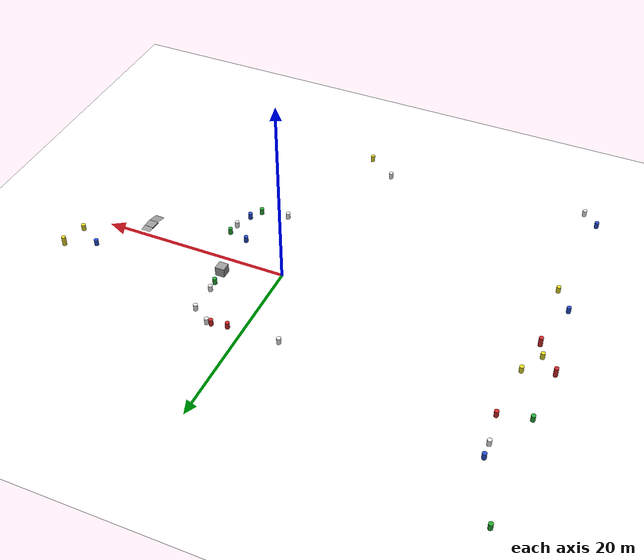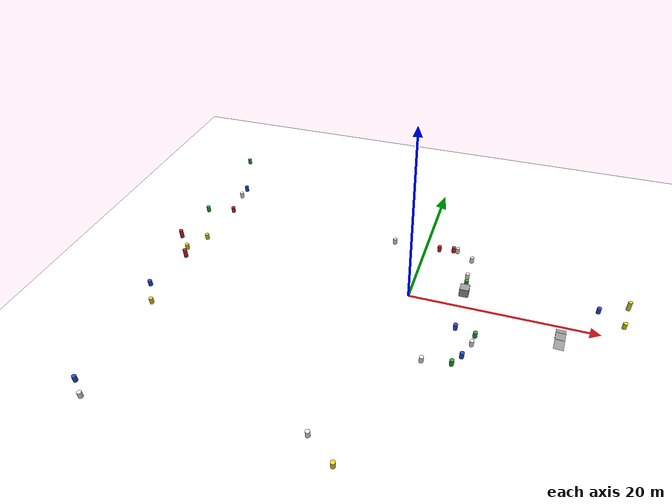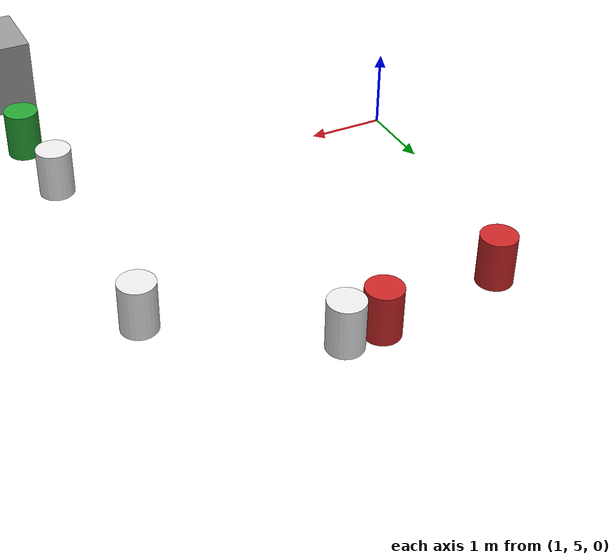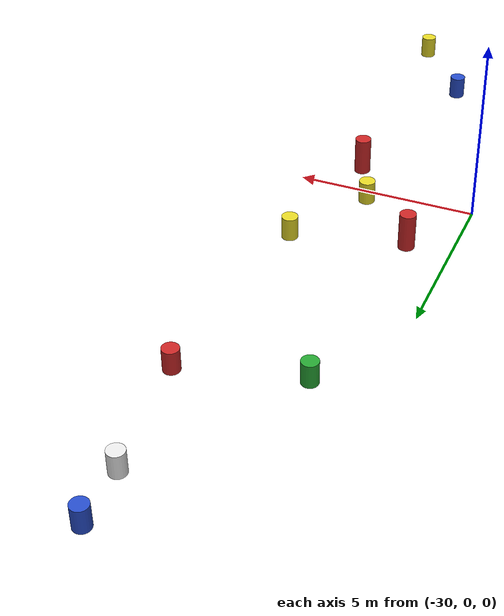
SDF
<sdf version="1.10">
 <world name="IGVC_AutoNav">
  <plugin name="gz::sim::systems::Physics" filename="gz-sim-physics-system"/>
  <plugin name="gz::sim::systems::UserCommands" filename="gz-sim-user-commands-system"/>
  <plugin name="gz::sim::systems::SceneBroadcaster" filename="gz-sim-scene-broadcaster-system"/>
  <plugin name="gz::sim::systems::Contact" filename="gz-sim-contact-system"/>
  <plugin name="gz::sim::systems::NavSat" filename="gz-sim-navsat-system"/>
  <spherical_coordinates>
   <surface_model>EARTH_WGS84</surface_model>
   <world_frame_orientation>ENU</world_frame_orientation>
   <latitude_deg>47.478949999999998</latitude_deg>
   <longitude_deg>19.057784999999999</longitude_deg>
   <elevation>0</elevation>
   <heading_deg>0</heading_deg>
  </spherical_coordinates>
  <plugin name="gz::sim::systems::Sensors" filename="gz-sim-sensors-system">
   <render_engine>ogre2</render_engine>
  </plugin>
  <plugin name="gz::sim::systems::Imu" filename="gz-sim-imu-system"/>
  <plugin name="gz::sim::systems::NavSat" filename="gz-sim-navsat-system"/>
  <gravity>0 0 -9.8000000000000007</gravity>
  <magnetic_field>6.0000000000000002e-06 2.3e-05 -4.1999999999999998e-05</magnetic_field>
  <atmosphere type="adiabatic"/>
  <physics type="ode">
   <max_step_size>0.001</max_step_size>
   <real_time_factor>1</real_time_factor>
   <real_time_update_rate>1000</real_time_update_rate>
  </physics>
  <scene>
   <ambient>0.400000006 0.400000006 0.400000006 1</ambient>
   <background>0.699999988 0.699999988 0.699999988 1</background>
   <shadows>true</shadows>
  </scene>
  <spherical_coordinates>
   <surface_model>EARTH_WGS84</surface_model>
   <latitude_deg>0</latitude_deg>
   <longitude_deg>0</longitude_deg>
   <elevation>0</elevation>
   <heading_deg>0</heading_deg>
  </spherical_coordinates>
  <model name="asphalt_ground_plane">
   <static>true</static>
   <link name="link">
    <collision name="collision">
     <geometry><plane><normal>0 0 1</normal><size>64.748999999999995 67.341999999999999</size></plane></geometry>
     <surface><friction><ode><mu>100</mu><mu2>50</mu2></ode></friction></surface>
    </collision>
    <visual name="visual">
     <cast_shadows>false</cast_shadows>
     <geometry><plane><normal>0 0 1</normal><size>64.748999999999995 67.341999999999999</size></plane></geometry>
     <material>
      <diffuse>1 1 1 1</diffuse>
      <specular>1 1 1 1</specular>
      <pbr><metal><albedo_map>file://media/materials/textures/asphalt.png</albedo_map></metal></pbr>
     </material>
    </visual>
    <inertial>
     <mass>1</mass>
     <inertia><ixx>1</ixx><ixy>0</ixy><ixz>0</ixz><iyy>1</iyy><iyz>0</iyz><izz>1</izz></inertia>
    </inertial>
   </link>
   <pose>0 7.095491886138916 0 0 0 0</pose>
  </model>
  <model name="barrel">
   <link name="link">
    <inertial>
     <mass>1</mass>
     <inertia>
      <ixx>0.14583299999999999</ixx>
      <ixy>0</ixy>
      <ixz>0</ixz>
      <iyy>0.14583299999999999</iyy>
      <iyz>0</iyz>
      <izz>0.125</izz>
     </inertia>
    </inertial>
    <visual name="visual">
     <geometry><cylinder><radius>0.222916</radius><length>1.0356700000000001</length></cylinder></geometry>
     <material>
      <script><name>Gazebo/Blue</name><uri>file://media/materials/scripts/gazebo.material</uri></script>
      <shader type="pixel"/>
     </material>
    </visual>
    <collision name="collision">
     <geometry><cylinder><radius>0.222916</radius><length>1.0356700000000001</length></cylinder></geometry>
     <surface>
      <friction>
       <ode><mu>1</mu><mu2>1</mu2><fdir1>0 0 0</fdir1><slip1>0</slip1><slip2>0</slip2></ode>
       <torsional>
        <coefficient>1</coefficient>
        <patch_radius>0</patch_radius>
        <surface_radius>0</surface_radius>
        <use_patch_radius>true</use_patch_radius>
        <ode><slip>0</slip></ode>
       </torsional>
      </friction>
      <bounce><restitution_coefficient>0</restitution_coefficient><threshold>1000000</threshold></bounce>
      <contact>
       <collide_without_contact>false</collide_without_contact>
       <collide_without_contact_bitmask>1</collide_without_contact_bitmask>
       <collide_bitmask>1</collide_bitmask>
       <ode>
        <soft_cfm>0</soft_cfm>
        <soft_erp>0.20000000000000001</soft_erp>
        <kp>10000000000000</kp>
        <kd>1</kd>
        <max_vel>0.01</max_vel>
        <min_depth>0</min_depth>
       </ode>
       <bullet>
        <split_impulse>true</split_impulse>
        <split_impulse_penetration_threshold>-0.01</split_impulse_penetration_threshold>
        <soft_cfm>0</soft_cfm>
        <soft_erp>0.20000000000000001</soft_erp>
        <kp>10000000000000</kp>
        <kd>1</kd>
       </bullet>
      </contact>
     </surface>
    </collision>
   </link>
   <static>false</static>
   <pose>7.06515 -6.9198300000000001 0.10701116576754102 7.4044332592144963e-18 1.7219624782401964e-16 1.8080497611149083e-19</pose>
  </model>
  <model name="barrel_0">
   <link name="link">
    <inertial>
     <mass>1</mass>
     <inertia>
      <ixx>0.14583299999999999</ixx>
      <ixy>0</ixy>
      <ixz>0</ixz>
      <iyy>0.14583299999999999</iyy>
      <iyz>0</iyz>
      <izz>0.125</izz>
     </inertia>
    </inertial>
    <visual name="visual">
     <geometry><cylinder><radius>0.222916</radius><length>1.0356700000000001</length></cylinder></geometry>
     <material>
      <script><name>Gazebo/Green</name><uri>file://media/materials/scripts/gazebo.material</uri></script>
      <shader type="pixel"/>
     </material>
    </visual>
    <collision name="collision">
     <geometry><cylinder><radius>0.222916</radius><length>1.0356700000000001</length></cylinder></geometry>
     <surface>
      <friction>
       <ode><mu>1</mu><mu2>1</mu2><fdir1>0 0 0</fdir1><slip1>0</slip1><slip2>0</slip2></ode>
       <torsional>
        <coefficient>1</coefficient>
        <patch_radius>0</patch_radius>
        <surface_radius>0</surface_radius>
        <use_patch_radius>true</use_patch_radius>
        <ode><slip>0</slip></ode>
       </torsional>
      </friction>
      <bounce><restitution_coefficient>0</restitution_coefficient><threshold>1000000</threshold></bounce>
      <contact>
       <collide_without_contact>false</collide_without_contact>
       <collide_without_contact_bitmask>1</collide_without_contact_bitmask>
       <collide_bitmask>1</collide_bitmask>
       <ode>
        <soft_cfm>0</soft_cfm>
        <soft_erp>0.20000000000000001</soft_erp>
        <kp>10000000000000</kp>
        <kd>1</kd>
        <max_vel>0.01</max_vel>
        <min_depth>0</min_depth>
       </ode>
       <bullet>
        <split_impulse>true</split_impulse>
        <split_impulse_penetration_threshold>-0.01</split_impulse_penetration_threshold>
        <soft_cfm>0</soft_cfm>
        <soft_erp>0.20000000000000001</soft_erp>
        <kp>10000000000000</kp>
        <kd>1</kd>
       </bullet>
      </contact>
     </surface>
    </collision>
   </link>
   <static>false</static>
   <pose>6.2997100000000001 -8.1233199999999997 0.1070131657332605 -1.157209345317784e-16 4.7496134980464341e-17 1.1440392333610301e-18</pose>
  </model>
  <model name="barrel_3">
   <link name="link">
    <inertial>
     <mass>1</mass>
     <inertia>
      <ixx>0.14583299999999999</ixx>
      <ixy>0</ixy>
      <ixz>0</ixz>
      <iyy>0.14583299999999999</iyy>
      <iyz>0</iyz>
      <izz>0.125</izz>
     </inertia>
    </inertial>
    <visual name="visual">
     <geometry><cylinder><radius>0.222916</radius><length>1.0356700000000001</length></cylinder></geometry>
     <material>
      <script><name>Gazebo/White</name><uri>file://media/materials/scripts/gazebo.material</uri></script>
      <shader type="pixel"/>
     </material>
    </visual>
    <collision name="collision">
     <geometry><cylinder><radius>0.222916</radius><length>1.0356700000000001</length></cylinder></geometry>
     <surface>
      <friction>
       <ode><mu>1</mu><mu2>1</mu2><fdir1>0 0 0</fdir1><slip1>0</slip1><slip2>0</slip2></ode>
       <torsional>
        <coefficient>1</coefficient>
        <patch_radius>0</patch_radius>
        <surface_radius>0</surface_radius>
        <use_patch_radius>true</use_patch_radius>
        <ode><slip>0</slip></ode>
       </torsional>
      </friction>
      <bounce><restitution_coefficient>0</restitution_coefficient><threshold>1000000</threshold></bounce>
      <contact>
       <collide_without_contact>false</collide_without_contact>
       <collide_without_contact_bitmask>1</collide_without_contact_bitmask>
       <collide_bitmask>1</collide_bitmask>
       <ode>
        <soft_cfm>0</soft_cfm>
        <soft_erp>0.20000000000000001</soft_erp>
        <kp>10000000000000</kp>
        <kd>1</kd>
        <max_vel>0.01</max_vel>
        <min_depth>0</min_depth>
       </ode>
       <bullet>
        <split_impulse>true</split_impulse>
        <split_impulse_penetration_threshold>-0.01</split_impulse_penetration_threshold>
        <soft_cfm>0</soft_cfm>
        <soft_erp>0.20000000000000001</soft_erp>
        <kp>10000000000000</kp>
        <kd>1</kd>
       </bullet>
      </contact>
     </surface>
    </collision>
   </link>
   <static>false</static>
   <pose>3.4230399999999999 -8.5684799999999992 0.10701516569897998 -1.1385295535115525e-16 -1.0134606897383649e-16 1.4112806861779908e-19</pose>
  </model>
  <model name="barrel_4">
   <link name="link">
    <inertial>
     <mass>1</mass>
     <inertia>
      <ixx>0.14583299999999999</ixx>
      <ixy>0</ixy>
      <ixz>0</ixz>
      <iyy>0.14583299999999999</iyy>
      <iyz>0</iyz>
      <izz>0.125</izz>
     </inertia>
    </inertial>
    <visual name="visual">
     <geometry><cylinder><radius>0.222916</radius><length>1.0356700000000001</length></cylinder></geometry>
     <material>
      <script><name>Gazebo/White</name><uri>file://media/materials/scripts/gazebo.material</uri></script>
      <shader type="pixel"/>
     </material>
    </visual>
    <collision name="collision">
     <geometry><cylinder><radius>0.222916</radius><length>1.0356700000000001</length></cylinder></geometry>
     <surface>
      <friction>
       <ode><mu>1</mu><mu2>1</mu2><fdir1>0 0 0</fdir1><slip1>0</slip1><slip2>0</slip2></ode>
       <torsional>
        <coefficient>1</coefficient>
        <patch_radius>0</patch_radius>
        <surface_radius>0</surface_radius>
        <use_patch_radius>true</use_patch_radius>
        <ode><slip>0</slip></ode>
       </torsional>
      </friction>
      <bounce><restitution_coefficient>0</restitution_coefficient><threshold>1000000</threshold></bounce>
      <contact>
       <collide_without_contact>false</collide_without_contact>
       <collide_without_contact_bitmask>1</collide_without_contact_bitmask>
       <collide_bitmask>1</collide_bitmask>
       <ode>
        <soft_cfm>0</soft_cfm>
        <soft_erp>0.20000000000000001</soft_erp>
        <kp>10000000000000</kp>
        <kd>1</kd>
        <max_vel>0.01</max_vel>
        <min_depth>0</min_depth>
       </ode>
       <bullet>
        <split_impulse>true</split_impulse>
        <split_impulse_penetration_threshold>-0.01</split_impulse_penetration_threshold>
        <soft_cfm>0</soft_cfm>
        <soft_erp>0.20000000000000001</soft_erp>
        <kp>10000000000000</kp>
        <kd>1</kd>
       </bullet>
      </contact>
     </surface>
    </collision>
   </link>
   <static>false</static>
   <pose>-25.243345260620117 -21.755100250244141 0.10567016181674294 1.7702595700880844e-16 2.1847962273575902e-17 -4.7314331793443644e-19</pose>
  </model>
  <model name="barrel_5">
   <link name="link">
    <inertial>
     <mass>1</mass>
     <inertia>
      <ixx>0.14583299999999999</ixx>
      <ixy>0</ixy>
      <ixz>0</ixz>
      <iyy>0.14583299999999999</iyy>
      <iyz>0</iyz>
      <izz>0.125</izz>
     </inertia>
    </inertial>
    <visual name="visual">
     <geometry><cylinder><radius>0.222916</radius><length>1.0356700000000001</length></cylinder></geometry>
     <material>
      <script><name>Gazebo/Yellow</name><uri>file://media/materials/scripts/gazebo.material</uri></script>
      <shader type="pixel"/>
     </material>
    </visual>
    <collision name="collision">
     <geometry><cylinder><radius>0.222916</radius><length>1.0356700000000001</length></cylinder></geometry>
     <surface>
      <friction>
       <ode><mu>1</mu><mu2>1</mu2><fdir1>0 0 0</fdir1><slip1>0</slip1><slip2>0</slip2></ode>
       <torsional>
        <coefficient>1</coefficient>
        <patch_radius>0</patch_radius>
        <surface_radius>0</surface_radius>
        <use_patch_radius>true</use_patch_radius>
        <ode><slip>0</slip></ode>
       </torsional>
      </friction>
      <bounce><restitution_coefficient>0</restitution_coefficient><threshold>1000000</threshold></bounce>
      <contact>
       <collide_without_contact>false</collide_without_contact>
       <collide_without_contact_bitmask>1</collide_without_contact_bitmask>
       <collide_bitmask>1</collide_bitmask>
       <ode>
        <soft_cfm>0</soft_cfm>
        <soft_erp>0.20000000000000001</soft_erp>
        <kp>10000000000000</kp>
        <kd>1</kd>
        <max_vel>0.01</max_vel>
        <min_depth>0</min_depth>
       </ode>
       <bullet>
        <split_impulse>true</split_impulse>
        <split_impulse_penetration_threshold>-0.01</split_impulse_penetration_threshold>
        <soft_cfm>0</soft_cfm>
        <soft_erp>0.20000000000000001</soft_erp>
        <kp>10000000000000</kp>
        <kd>1</kd>
       </bullet>
      </contact>
     </surface>
    </collision>
   </link>
   <static>false</static>
   <pose>-25.960578918457031 -8.9916601181030273 0.1065161812272063 2.6867724805789714e-17 3.0815322531723578e-17 2.2916971820285563e-19</pose>
  </model>
  <model name="barrel_7">
   <link name="link">
    <inertial>
     <mass>1</mass>
     <inertia>
      <ixx>0.14583299999999999</ixx>
      <ixy>0</ixy>
      <ixz>0</ixz>
      <iyy>0.14583299999999999</iyy>
      <iyz>0</iyz>
      <izz>0.125</izz>
     </inertia>
    </inertial>
    <visual name="visual">
     <geometry><cylinder><radius>0.222916</radius><length>1.0356700000000001</length></cylinder></geometry>
     <material>
      <script><name>Gazebo/Blue</name><uri>file://media/materials/scripts/gazebo.material</uri></script>
      <shader type="pixel"/>
     </material>
    </visual>
    <collision name="collision">
     <geometry><cylinder><radius>0.222916</radius><length>1.0356700000000001</length></cylinder></geometry>
     <surface>
      <friction>
       <ode><mu>1</mu><mu2>1</mu2><fdir1>0 0 0</fdir1><slip1>0</slip1><slip2>0</slip2></ode>
       <torsional>
        <coefficient>1</coefficient>
        <patch_radius>0</patch_radius>
        <surface_radius>0</surface_radius>
        <use_patch_radius>true</use_patch_radius>
        <ode><slip>0</slip></ode>
       </torsional>
      </friction>
      <bounce><restitution_coefficient>0</restitution_coefficient><threshold>1000000</threshold></bounce>
      <contact>
       <collide_without_contact>false</collide_without_contact>
       <collide_without_contact_bitmask>1</collide_without_contact_bitmask>
       <collide_bitmask>1</collide_bitmask>
       <ode>
        <soft_cfm>0</soft_cfm>
        <soft_erp>0.20000000000000001</soft_erp>
        <kp>10000000000000</kp>
        <kd>1</kd>
        <max_vel>0.01</max_vel>
        <min_depth>0</min_depth>
       </ode>
       <bullet>
        <split_impulse>true</split_impulse>
        <split_impulse_penetration_threshold>-0.01</split_impulse_penetration_threshold>
        <soft_cfm>0</soft_cfm>
        <soft_erp>0.20000000000000001</soft_erp>
        <kp>10000000000000</kp>
        <kd>1</kd>
       </bullet>
      </contact>
     </surface>
    </collision>
   </link>
   <static>false</static>
   <pose>-27.665267944335938 -6.5483798980712891 0.10637216365884961 -6.2391428076182949e-17 -1.6038522733634272e-16 -1.9421049059180795e-19</pose>
  </model>
  <model name="barrel_8">
   <link name="link">
    <inertial>
     <mass>1</mass>
     <inertia>
      <ixx>0.14583299999999999</ixx>
      <ixy>0</ixy>
      <ixz>0</ixz>
      <iyy>0.14583299999999999</iyy>
      <iyz>0</iyz>
      <izz>0.125</izz>
     </inertia>
    </inertial>
    <visual name="visual">
     <geometry><cylinder><radius>0.222916</radius><length>1.0356700000000001</length></cylinder></geometry>
     <material>
      <script><name>Gazebo/White</name><uri>file://media/materials/scripts/gazebo.material</uri></script>
      <shader type="pixel"/>
     </material>
    </visual>
    <collision name="collision">
     <geometry><cylinder><radius>0.222916</radius><length>1.0356700000000001</length></cylinder></geometry>
     <surface>
      <friction>
       <ode><mu>1</mu><mu2>1</mu2><fdir1>0 0 0</fdir1><slip1>0</slip1><slip2>0</slip2></ode>
       <torsional>
        <coefficient>1</coefficient>
        <patch_radius>0</patch_radius>
        <surface_radius>0</surface_radius>
        <use_patch_radius>true</use_patch_radius>
        <ode><slip>0</slip></ode>
       </torsional>
      </friction>
      <bounce><restitution_coefficient>0</restitution_coefficient><threshold>1000000</threshold></bounce>
      <contact>
       <collide_without_contact>false</collide_without_contact>
       <collide_without_contact_bitmask>1</collide_without_contact_bitmask>
       <collide_bitmask>1</collide_bitmask>
       <ode>
        <soft_cfm>0</soft_cfm>
        <soft_erp>0.20000000000000001</soft_erp>
        <kp>10000000000000</kp>
        <kd>1</kd>
        <max_vel>0.01</max_vel>
        <min_depth>0</min_depth>
       </ode>
       <bullet>
        <split_impulse>true</split_impulse>
        <split_impulse_penetration_threshold>-0.01</split_impulse_penetration_threshold>
        <soft_cfm>0</soft_cfm>
        <soft_erp>0.20000000000000001</soft_erp>
        <kp>10000000000000</kp>
        <kd>1</kd>
       </bullet>
      </contact>
     </surface>
    </collision>
   </link>
   <static>false</static>
   <pose>-3.9541099071502686 -19.554193496704102 0.10605222830741357 -9.3730669206002352e-17 -1.6683673459121081e-16 -3.918224371357502e-19</pose>
  </model>
  <model name="barrel_10">
   <link name="link">
    <inertial>
     <mass>1</mass>
     <inertia>
      <ixx>0.14583299999999999</ixx>
      <ixy>0</ixy>
      <ixz>0</ixz>
      <iyy>0.14583299999999999</iyy>
      <iyz>0</iyz>
      <izz>0.125</izz>
     </inertia>
    </inertial>
    <visual name="visual">
     <geometry><cylinder><radius>0.222916</radius><length>1.0356700000000001</length></cylinder></geometry>
     <material>
      <script><name>Gazebo/Blue</name><uri>file://media/materials/scripts/gazebo.material</uri></script>
      <shader type="pixel"/>
     </material>
    </visual>
    <collision name="collision">
     <geometry><cylinder><radius>0.222916</radius><length>1.0356700000000001</length></cylinder></geometry>
     <surface>
      <friction>
       <ode><mu>1</mu><mu2>1</mu2><fdir1>0 0 0</fdir1><slip1>0</slip1><slip2>0</slip2></ode>
       <torsional>
        <coefficient>1</coefficient>
        <patch_radius>0</patch_radius>
        <surface_radius>0</surface_radius>
        <use_patch_radius>true</use_patch_radius>
        <ode><slip>0</slip></ode>
       </torsional>
      </friction>
      <bounce><restitution_coefficient>0</restitution_coefficient><threshold>1000000</threshold></bounce>
      <contact>
       <collide_without_contact>false</collide_without_contact>
       <collide_without_contact_bitmask>1</collide_without_contact_bitmask>
       <collide_bitmask>1</collide_bitmask>
       <ode>
        <soft_cfm>0</soft_cfm>
        <soft_erp>0.20000000000000001</soft_erp>
        <kp>10000000000000</kp>
        <kd>1</kd>
        <max_vel>0.01</max_vel>
        <min_depth>0</min_depth>
       </ode>
       <bullet>
        <split_impulse>true</split_impulse>
        <split_impulse_penetration_threshold>-0.01</split_impulse_penetration_threshold>
        <soft_cfm>0</soft_cfm>
        <soft_erp>0.20000000000000001</soft_erp>
        <kp>10000000000000</kp>
        <kd>1</kd>
       </bullet>
      </contact>
     </surface>
    </collision>
   </link>
   <static>false</static>
   <pose>-25.850784301757812 13.89840030670166 0.10622122363706199 -2.3725561040519514e-16 7.8936602894727486e-17 1.0374188059436404e-19</pose>
  </model>
  <model name="barrel_11">
   <link name="link">
    <inertial>
     <mass>1</mass>
     <inertia>
      <ixx>0.14583299999999999</ixx>
      <ixy>0</ixy>
      <ixz>0</ixz>
      <iyy>0.14583299999999999</iyy>
      <iyz>0</iyz>
      <izz>0.125</izz>
     </inertia>
    </inertial>
    <visual name="visual">
     <geometry><cylinder><radius>0.222916</radius><length>1.0356700000000001</length></cylinder></geometry>
     <material>
      <script><name>Gazebo/Yellow</name><uri>file://media/materials/scripts/gazebo.material</uri></script>
      <shader type="pixel"/>
     </material>
    </visual>
    <collision name="collision">
     <geometry><cylinder><radius>0.222916</radius><length>1.0356700000000001</length></cylinder></geometry>
     <surface>
      <friction>
       <ode><mu>1</mu><mu2>1</mu2><fdir1>0 0 0</fdir1><slip1>0</slip1><slip2>0</slip2></ode>
       <torsional>
        <coefficient>1</coefficient>
        <patch_radius>0</patch_radius>
        <surface_radius>0</surface_radius>
        <use_patch_radius>true</use_patch_radius>
        <ode><slip>0</slip></ode>
       </torsional>
      </friction>
      <bounce><restitution_coefficient>0</restitution_coefficient><threshold>1000000</threshold></bounce>
      <contact>
       <collide_without_contact>false</collide_without_contact>
       <collide_without_contact_bitmask>1</collide_without_contact_bitmask>
       <collide_bitmask>1</collide_bitmask>
       <ode>
        <soft_cfm>0</soft_cfm>
        <soft_erp>0.20000000000000001</soft_erp>
        <kp>10000000000000</kp>
        <kd>1</kd>
        <max_vel>0.01</max_vel>
        <min_depth>0</min_depth>
       </ode>
       <bullet>
        <split_impulse>true</split_impulse>
        <split_impulse_penetration_threshold>-0.01</split_impulse_penetration_threshold>
        <soft_cfm>0</soft_cfm>
        <soft_erp>0.20000000000000001</soft_erp>
        <kp>10000000000000</kp>
        <kd>1</kd>
       </bullet>
      </contact>
     </surface>
    </collision>
   </link>
   <static>false</static>
   <pose>-27.086606979370117 0.41173800826072693 0.10645019625719832 -1.3037009990999045e-16 1.7900994305488219e-17 -7.0423757184633342e-19</pose>
  </model>
  <model name="barrel_13">
   <link name="link">
    <inertial>
     <mass>1</mass>
     <inertia>
      <ixx>0.14583299999999999</ixx>
      <ixy>0</ixy>
      <ixz>0</ixz>
      <iyy>0.14583299999999999</iyy>
      <iyz>0</iyz>
      <izz>0.125</izz>
     </inertia>
    </inertial>
    <visual name="visual">
     <geometry><cylinder><radius>0.222916</radius><length>1.0356700000000001</length></cylinder></geometry>
     <material>
      <script><name>Gazebo/Green</name><uri>file://media/materials/scripts/gazebo.material</uri></script>
      <shader type="pixel"/>
     </material>
    </visual>
    <collision name="collision">
     <geometry><cylinder><radius>0.222916</radius><length>1.0356700000000001</length></cylinder></geometry>
     <surface>
      <friction>
       <ode><mu>1</mu><mu2>1</mu2><fdir1>0 0 0</fdir1><slip1>0</slip1><slip2>0</slip2></ode>
       <torsional>
        <coefficient>1</coefficient>
        <patch_radius>0</patch_radius>
        <surface_radius>0</surface_radius>
        <use_patch_radius>true</use_patch_radius>
        <ode><slip>0</slip></ode>
       </torsional>
      </friction>
      <bounce><restitution_coefficient>0</restitution_coefficient><threshold>1000000</threshold></bounce>
      <contact>
       <collide_without_contact>false</collide_without_contact>
       <collide_without_contact_bitmask>1</collide_without_contact_bitmask>
       <collide_bitmask>1</collide_bitmask>
       <ode>
        <soft_cfm>0</soft_cfm>
        <soft_erp>0.20000000000000001</soft_erp>
        <kp>10000000000000</kp>
        <kd>1</kd>
        <max_vel>0.01</max_vel>
        <min_depth>0</min_depth>
       </ode>
       <bullet>
        <split_impulse>true</split_impulse>
        <split_impulse_penetration_threshold>-0.01</split_impulse_penetration_threshold>
        <soft_cfm>0</soft_cfm>
        <soft_erp>0.20000000000000001</soft_erp>
        <kp>10000000000000</kp>
        <kd>1</kd>
       </bullet>
      </contact>
     </surface>
    </collision>
   </link>
   <static>false</static>
   <pose>-28.592302322387695 20.560400009155273 0.10600714913253106 1.8420373447517376e-16 -3.2789498737238188e-18 -1.278068026831369e-18</pose>
  </model>
  <model name="barrel_14">
   <link name="link">
    <inertial>
     <mass>1</mass>
     <inertia>
      <ixx>0.14583299999999999</ixx>
      <ixy>0</ixy>
      <ixz>0</ixz>
      <iyy>0.14583299999999999</iyy>
      <iyz>0</iyz>
      <izz>0.125</izz>
     </inertia>
    </inertial>
    <visual name="visual">
     <geometry><cylinder><radius>0.222916</radius><length>1.0356700000000001</length></cylinder></geometry>
     <material>
      <script><name>Gazebo/Red</name><uri>file://media/materials/scripts/gazebo.material</uri></script>
      <shader type="pixel"/>
     </material>
    </visual>
    <collision name="collision">
     <geometry><cylinder><radius>0.222916</radius><length>1.0356700000000001</length></cylinder></geometry>
     <surface>
      <friction>
       <ode><mu>1</mu><mu2>1</mu2><fdir1>0 0 0</fdir1><slip1>0</slip1><slip2>0</slip2></ode>
       <torsional>
        <coefficient>1</coefficient>
        <patch_radius>0</patch_radius>
        <surface_radius>0</surface_radius>
        <use_patch_radius>true</use_patch_radius>
        <ode><slip>0</slip></ode>
       </torsional>
      </friction>
      <bounce><restitution_coefficient>0</restitution_coefficient><threshold>1000000</threshold></bounce>
      <contact>
       <collide_without_contact>false</collide_without_contact>
       <collide_without_contact_bitmask>1</collide_without_contact_bitmask>
       <collide_bitmask>1</collide_bitmask>
       <ode>
        <soft_cfm>0</soft_cfm>
        <soft_erp>0.20000000000000001</soft_erp>
        <kp>10000000000000</kp>
        <kd>1</kd>
        <max_vel>0.01</max_vel>
        <min_depth>0</min_depth>
       </ode>
       <bullet>
        <split_impulse>true</split_impulse>
        <split_impulse_penetration_threshold>-0.01</split_impulse_penetration_threshold>
        <soft_cfm>0</soft_cfm>
        <soft_erp>0.20000000000000001</soft_erp>
        <kp>10000000000000</kp>
        <kd>1</kd>
       </bullet>
      </contact>
     </surface>
    </collision>
   </link>
   <static>false</static>
   <pose>-25.332365036010742 8.9310302734375 0.10622715459722809 -6.6675818667961086e-17 -1.0219379022081421e-16 8.7290005640982418e-21</pose>
  </model>
  <model name="barrel_15">
   <link name="link">
    <inertial>
     <mass>1</mass>
     <inertia>
      <ixx>0.14583299999999999</ixx>
      <ixy>0</ixy>
      <ixz>0</ixz>
      <iyy>0.14583299999999999</iyy>
      <iyz>0</iyz>
      <izz>0.125</izz>
     </inertia>
    </inertial>
    <visual name="visual">
     <geometry><cylinder><radius>0.222916</radius><length>1.0356700000000001</length></cylinder></geometry>
     <material>
      <script><name>Gazebo/White</name><uri>file://media/materials/scripts/gazebo.material</uri></script>
      <shader type="pixel"/>
     </material>
    </visual>
    <collision name="collision">
     <geometry><cylinder><radius>0.222916</radius><length>1.0356700000000001</length></cylinder></geometry>
     <surface>
      <friction>
       <ode><mu>1</mu><mu2>1</mu2><fdir1>0 0 0</fdir1><slip1>0</slip1><slip2>0</slip2></ode>
       <torsional>
        <coefficient>1</coefficient>
        <patch_radius>0</patch_radius>
        <surface_radius>0</surface_radius>
        <use_patch_radius>true</use_patch_radius>
        <ode><slip>0</slip></ode>
       </torsional>
      </friction>
      <bounce><restitution_coefficient>0</restitution_coefficient><threshold>1000000</threshold></bounce>
      <contact>
       <collide_without_contact>false</collide_without_contact>
       <collide_without_contact_bitmask>1</collide_without_contact_bitmask>
       <collide_bitmask>1</collide_bitmask>
       <ode>
        <soft_cfm>0</soft_cfm>
        <soft_erp>0.20000000000000001</soft_erp>
        <kp>10000000000000</kp>
        <kd>1</kd>
        <max_vel>0.01</max_vel>
        <min_depth>0</min_depth>
       </ode>
       <bullet>
        <split_impulse>true</split_impulse>
        <split_impulse_penetration_threshold>-0.01</split_impulse_penetration_threshold>
        <soft_cfm>0</soft_cfm>
        <soft_erp>0.20000000000000001</soft_erp>
        <kp>10000000000000</kp>
        <kd>1</kd>
       </bullet>
      </contact>
     </surface>
    </collision>
   </link>
   <static>false</static>
   <pose>-25.783918380737305 12.307399749755859 0.10629118058315268 -2.3549194196413882e-16 -7.2279924073208308e-17 -1.8686154239813113e-19</pose>
  </model>
  <model name="barrel_16">
   <link name="link">
    <inertial>
     <mass>1</mass>
     <inertia>
      <ixx>0.14583299999999999</ixx>
      <ixy>0</ixy>
      <ixz>0</ixz>
      <iyy>0.14583299999999999</iyy>
      <iyz>0</iyz>
      <izz>0.125</izz>
     </inertia>
    </inertial>
    <visual name="visual">
     <geometry><cylinder><radius>0.222916</radius><length>1.0356700000000001</length></cylinder></geometry>
     <material>
      <script><name>Gazebo/Yellow</name><uri>file://media/materials/scripts/gazebo.material</uri></script>
      <shader type="pixel"/>
     </material>
    </visual>
    <collision name="collision">
     <geometry><cylinder><radius>0.222916</radius><length>1.0356700000000001</length></cylinder></geometry>
     <surface>
      <friction>
       <ode><mu>1</mu><mu2>1</mu2><fdir1>0 0 0</fdir1><slip1>0</slip1><slip2>0</slip2></ode>
       <torsional>
        <coefficient>1</coefficient>
        <patch_radius>0</patch_radius>
        <surface_radius>0</surface_radius>
        <use_patch_radius>true</use_patch_radius>
        <ode><slip>0</slip></ode>
       </torsional>
      </friction>
      <bounce><restitution_coefficient>0</restitution_coefficient><threshold>1000000</threshold></bounce>
      <contact>
       <collide_without_contact>false</collide_without_contact>
       <collide_without_contact_bitmask>1</collide_without_contact_bitmask>
       <collide_bitmask>1</collide_bitmask>
       <ode>
        <soft_cfm>0</soft_cfm>
        <soft_erp>0.20000000000000001</soft_erp>
        <kp>10000000000000</kp>
        <kd>1</kd>
        <max_vel>0.01</max_vel>
        <min_depth>0</min_depth>
       </ode>
       <bullet>
        <split_impulse>true</split_impulse>
        <split_impulse_penetration_threshold>-0.01</split_impulse_penetration_threshold>
        <soft_cfm>0</soft_cfm>
        <soft_erp>0.20000000000000001</soft_erp>
        <kp>10000000000000</kp>
        <kd>1</kd>
       </bullet>
      </contact>
     </surface>
    </collision>
   </link>
   <static>false</static>
   <pose>-25.781974792480469 2.863569974899292 0.10612014297599803 -1.3077373448423808e-16 1.7892124913556642e-16 -7.2979554738805974e-20</pose>
  </model>
  <model name="barrel_22">
   <link name="link">
    <inertial>
     <mass>1</mass>
     <inertia>
      <ixx>0.14583299999999999</ixx>
      <ixy>0</ixy>
      <ixz>0</ixz>
      <iyy>0.14583299999999999</iyy>
      <iyz>0</iyz>
      <izz>0.125</izz>
     </inertia>
    </inertial>
    <visual name="visual">
     <geometry><cylinder><radius>0.222916</radius><length>1.0356700000000001</length></cylinder></geometry>
     <material>
      <script><name>Gazebo/White</name><uri>file://media/materials/scripts/gazebo.material</uri></script>
      <shader type="pixel"/>
     </material>
    </visual>
    <collision name="collision">
     <geometry><cylinder><radius>0.222916</radius><length>1.0356700000000001</length></cylinder></geometry>
     <surface>
      <friction>
       <ode><mu>1</mu><mu2>1</mu2><fdir1>0 0 0</fdir1><slip1>0</slip1><slip2>0</slip2></ode>
       <torsional>
        <coefficient>1</coefficient>
        <patch_radius>0</patch_radius>
        <surface_radius>0</surface_radius>
        <use_patch_radius>true</use_patch_radius>
        <ode><slip>0</slip></ode>
       </torsional>
      </friction>
      <bounce><restitution_coefficient>0</restitution_coefficient><threshold>1000000</threshold></bounce>
      <contact>
       <collide_without_contact>false</collide_without_contact>
       <collide_without_contact_bitmask>1</collide_without_contact_bitmask>
       <collide_bitmask>1</collide_bitmask>
       <ode>
        <soft_cfm>0</soft_cfm>
        <soft_erp>0.20000000000000001</soft_erp>
        <kp>10000000000000</kp>
        <kd>1</kd>
        <max_vel>0.01</max_vel>
        <min_depth>0</min_depth>
       </ode>
       <bullet>
        <split_impulse>true</split_impulse>
        <split_impulse_penetration_threshold>-0.01</split_impulse_penetration_threshold>
        <soft_cfm>0</soft_cfm>
        <soft_erp>0.20000000000000001</soft_erp>
        <kp>10000000000000</kp>
        <kd>1</kd>
       </bullet>
      </contact>
     </surface>
    </collision>
   </link>
   <static>false</static>
   <pose>-3.8054899999999998 8.6114200000000007 0.10703916528761373 -1.5741481008698967e-17 1.8536295571224748e-17 1.2595638624590259e-18</pose>
  </model>
  <model name="barrel_23">
   <link name="link">
    <inertial>
     <mass>1</mass>
     <inertia>
      <ixx>0.14583299999999999</ixx>
      <ixy>0</ixy>
      <ixz>0</ixz>
      <iyy>0.14583299999999999</iyy>
      <iyz>0</iyz>
      <izz>0.125</izz>
     </inertia>
    </inertial>
    <visual name="visual">
     <geometry><cylinder><radius>0.222916</radius><length>1.0356700000000001</length></cylinder></geometry>
     <material>
      <script><name>Gazebo/Green</name><uri>file://media/materials/scripts/gazebo.material</uri></script>
      <shader type="pixel"/>
     </material>
    </visual>
    <collision name="collision">
     <geometry><cylinder><radius>0.222916</radius><length>1.0356700000000001</length></cylinder></geometry>
     <surface>
      <friction>
       <ode><mu>1</mu><mu2>1</mu2><fdir1>0 0 0</fdir1><slip1>0</slip1><slip2>0</slip2></ode>
       <torsional>
        <coefficient>1</coefficient>
        <patch_radius>0</patch_radius>
        <surface_radius>0</surface_radius>
        <use_patch_radius>true</use_patch_radius>
        <ode><slip>0</slip></ode>
       </torsional>
      </friction>
      <bounce><restitution_coefficient>0</restitution_coefficient><threshold>1000000</threshold></bounce>
      <contact>
       <collide_without_contact>false</collide_without_contact>
       <collide_without_contact_bitmask>1</collide_without_contact_bitmask>
       <collide_bitmask>1</collide_bitmask>
       <ode>
        <soft_cfm>0</soft_cfm>
        <soft_erp>0.20000000000000001</soft_erp>
        <kp>10000000000000</kp>
        <kd>1</kd>
        <max_vel>0.01</max_vel>
        <min_depth>0</min_depth>
       </ode>
       <bullet>
        <split_impulse>true</split_impulse>
        <split_impulse_penetration_threshold>-0.01</split_impulse_penetration_threshold>
        <soft_cfm>0</soft_cfm>
        <soft_erp>0.20000000000000001</soft_erp>
        <kp>10000000000000</kp>
        <kd>1</kd>
       </bullet>
      </contact>
     </surface>
    </collision>
   </link>
   <static>false</static>
   <pose>-28.454685211181641 8.1344699859619141 0.10606422389878933 -7.5327246992345499e-17 3.8921383445271201e-17 -4.0529536450749593e-19</pose>
  </model>
  <model name="barrel_24">
   <link name="link">
    <inertial>
     <mass>1</mass>
     <inertia>
      <ixx>0.14583299999999999</ixx>
      <ixy>0</ixy>
      <ixz>0</ixz>
      <iyy>0.14583299999999999</iyy>
      <iyz>0</iyz>
      <izz>0.125</izz>
     </inertia>
    </inertial>
    <visual name="visual">
     <geometry><cylinder><radius>0.222916</radius><length>1.0356700000000001</length></cylinder></geometry>
     <material>
      <script><name>Gazebo/White</name><uri>file://media/materials/scripts/gazebo.material</uri></script>
      <shader type="pixel"/>
     </material>
    </visual>
    <collision name="collision">
     <geometry><cylinder><radius>0.222916</radius><length>1.0356700000000001</length></cylinder></geometry>
     <surface>
      <friction>
       <ode><mu>1</mu><mu2>1</mu2><fdir1>0 0 0</fdir1><slip1>0</slip1><slip2>0</slip2></ode>
       <torsional>
        <coefficient>1</coefficient>
        <patch_radius>0</patch_radius>
        <surface_radius>0</surface_radius>
        <use_patch_radius>true</use_patch_radius>
        <ode><slip>0</slip></ode>
       </torsional>
      </friction>
      <bounce><restitution_coefficient>0</restitution_coefficient><threshold>1000000</threshold></bounce>
      <contact>
       <collide_without_contact>false</collide_without_contact>
       <collide_without_contact_bitmask>1</collide_without_contact_bitmask>
       <collide_bitmask>1</collide_bitmask>
       <ode>
        <soft_cfm>0</soft_cfm>
        <soft_erp>0.20000000000000001</soft_erp>
        <kp>10000000000000</kp>
        <kd>1</kd>
        <max_vel>0.01</max_vel>
        <min_depth>0</min_depth>
       </ode>
       <bullet>
        <split_impulse>true</split_impulse>
        <split_impulse_penetration_threshold>-0.01</split_impulse_penetration_threshold>
        <soft_cfm>0</soft_cfm>
        <soft_erp>0.20000000000000001</soft_erp>
        <kp>10000000000000</kp>
        <kd>1</kd>
       </bullet>
      </contact>
     </surface>
    </collision>
   </link>
   <static>false</static>
   <pose>5.5689799999999998 7.7809699999999999 0.10704316521905269 -9.7909261086596481e-17 -1.6874608648344901e-16 3.6073992035923793e-19</pose>
  </model>
  <model name="barrel_26">
   <link name="link">
    <inertial>
     <mass>1</mass>
     <inertia>
      <ixx>0.14583299999999999</ixx>
      <ixy>0</ixy>
      <ixz>0</ixz>
      <iyy>0.14583299999999999</iyy>
      <iyz>0</iyz>
      <izz>0.125</izz>
     </inertia>
    </inertial>
    <visual name="visual">
     <geometry><cylinder><radius>0.222916</radius><length>1.0356700000000001</length></cylinder></geometry>
     <material>
      <script><name>Gazebo/Red</name><uri>file://media/materials/scripts/gazebo.material</uri></script>
      <shader type="pixel"/>
     </material>
    </visual>
    <collision name="collision">
     <geometry><cylinder><radius>0.222916</radius><length>1.0356700000000001</length></cylinder></geometry>
     <surface>
      <friction>
       <ode><mu>1</mu><mu2>1</mu2><fdir1>0 0 0</fdir1><slip1>0</slip1><slip2>0</slip2></ode>
       <torsional>
        <coefficient>1</coefficient>
        <patch_radius>0</patch_radius>
        <surface_radius>0</surface_radius>
        <use_patch_radius>true</use_patch_radius>
        <ode><slip>0</slip></ode>
       </torsional>
      </friction>
      <bounce><restitution_coefficient>0</restitution_coefficient><threshold>1000000</threshold></bounce>
      <contact>
       <collide_without_contact>false</collide_without_contact>
       <collide_without_contact_bitmask>1</collide_without_contact_bitmask>
       <collide_bitmask>1</collide_bitmask>
       <ode>
        <soft_cfm>0</soft_cfm>
        <soft_erp>0.20000000000000001</soft_erp>
        <kp>10000000000000</kp>
        <kd>1</kd>
        <max_vel>0.01</max_vel>
        <min_depth>0</min_depth>
       </ode>
       <bullet>
        <split_impulse>true</split_impulse>
        <split_impulse_penetration_threshold>-0.01</split_impulse_penetration_threshold>
        <soft_cfm>0</soft_cfm>
        <soft_erp>0.20000000000000001</soft_erp>
        <kp>10000000000000</kp>
        <kd>1</kd>
       </bullet>
      </contact>
     </surface>
    </collision>
   </link>
   <static>false</static>
   <pose>1.5857000000000001 8.7365399999999998 0.10704516518477217 2.5249399236442983e-17 1.388229825401837e-16 1.481047465622183e-18</pose>
  </model>
  <model name="barrel_27">
   <link name="link">
    <inertial>
     <mass>1</mass>
     <inertia>
      <ixx>0.14583299999999999</ixx>
      <ixy>0</ixy>
      <ixz>0</ixz>
      <iyy>0.14583299999999999</iyy>
      <iyz>0</iyz>
      <izz>0.125</izz>
     </inertia>
    </inertial>
    <visual name="visual">
     <geometry><cylinder><radius>0.222916</radius><length>1.0356700000000001</length></cylinder></geometry>
     <material>
      <script><name>Gazebo/Red</name><uri>file://media/materials/scripts/gazebo.material</uri></script>
      <shader type="pixel"/>
     </material>
    </visual>
    <collision name="collision">
     <geometry><cylinder><radius>0.222916</radius><length>1.0356700000000001</length></cylinder></geometry>
     <surface>
      <friction>
       <ode><mu>1</mu><mu2>1</mu2><fdir1>0 0 0</fdir1><slip1>0</slip1><slip2>0</slip2></ode>
       <torsional>
        <coefficient>1</coefficient>
        <patch_radius>0</patch_radius>
        <surface_radius>0</surface_radius>
        <use_patch_radius>true</use_patch_radius>
        <ode><slip>0</slip></ode>
       </torsional>
      </friction>
      <bounce><restitution_coefficient>0</restitution_coefficient><threshold>1000000</threshold></bounce>
      <contact>
       <collide_without_contact>false</collide_without_contact>
       <collide_without_contact_bitmask>1</collide_without_contact_bitmask>
       <collide_bitmask>1</collide_bitmask>
       <ode>
        <soft_cfm>0</soft_cfm>
        <soft_erp>0.20000000000000001</soft_erp>
        <kp>10000000000000</kp>
        <kd>1</kd>
        <max_vel>0.01</max_vel>
        <min_depth>0</min_depth>
       </ode>
       <bullet>
        <split_impulse>true</split_impulse>
        <split_impulse_penetration_threshold>-0.01</split_impulse_penetration_threshold>
        <soft_cfm>0</soft_cfm>
        <soft_erp>0.20000000000000001</soft_erp>
        <kp>10000000000000</kp>
        <kd>1</kd>
       </bullet>
      </contact>
     </surface>
    </collision>
   </link>
   <static>false</static>
   <pose>3.2216999999999998 9.0043100000000003 0.10704716515049165 -2.1990650078509022e-16 -2.2904649029452029e-17 1.7148494676408444e-18</pose>
  </model>
  <model name="barrel_28">
   <link name="link">
    <inertial>
     <mass>1</mass>
     <inertia>
      <ixx>0.14583299999999999</ixx>
      <ixy>0</ixy>
      <ixz>0</ixz>
      <iyy>0.14583299999999999</iyy>
      <iyz>0</iyz>
      <izz>0.125</izz>
     </inertia>
    </inertial>
    <visual name="visual">
     <geometry><cylinder><radius>0.222916</radius><length>1.0356700000000001</length></cylinder></geometry>
     <material>
      <script><name>Gazebo/White</name><uri>file://media/materials/scripts/gazebo.material</uri></script>
      <shader type="pixel"/>
     </material>
    </visual>
    <collision name="collision">
     <geometry><cylinder><radius>0.222916</radius><length>1.0356700000000001</length></cylinder></geometry>
     <surface>
      <friction>
       <ode><mu>1</mu><mu2>1</mu2><fdir1>0 0 0</fdir1><slip1>0</slip1><slip2>0</slip2></ode>
       <torsional>
        <coefficient>1</coefficient>
        <patch_radius>0</patch_radius>
        <surface_radius>0</surface_radius>
        <use_patch_radius>true</use_patch_radius>
        <ode><slip>0</slip></ode>
       </torsional>
      </friction>
      <bounce><restitution_coefficient>0</restitution_coefficient><threshold>1000000</threshold></bounce>
      <contact>
       <collide_without_contact>false</collide_without_contact>
       <collide_without_contact_bitmask>1</collide_without_contact_bitmask>
       <collide_bitmask>1</collide_bitmask>
       <ode>
        <soft_cfm>0</soft_cfm>
        <soft_erp>0.20000000000000001</soft_erp>
        <kp>10000000000000</kp>
        <kd>1</kd>
        <max_vel>0.01</max_vel>
        <min_depth>0</min_depth>
       </ode>
       <bullet>
        <split_impulse>true</split_impulse>
        <split_impulse_penetration_threshold>-0.01</split_impulse_penetration_threshold>
        <soft_cfm>0</soft_cfm>
        <soft_erp>0.20000000000000001</soft_erp>
        <kp>10000000000000</kp>
        <kd>1</kd>
       </bullet>
      </contact>
     </surface>
    </collision>
   </link>
   <static>false</static>
   <pose>3.68913 9.0244900000000001 0.10704916511621113 -1.2033052093565336e-16 -2.3522137488015187e-16 -3.1454808388678424e-19</pose>
  </model>
  <model name="barrel_30">
   <link name="link">
    <inertial>
     <mass>1</mass>
     <inertia>
      <ixx>0.14583299999999999</ixx>
      <ixy>0</ixy>
      <ixz>0</ixz>
      <iyy>0.14583299999999999</iyy>
      <iyz>0</iyz>
      <izz>0.125</izz>
     </inertia>
    </inertial>
    <visual name="visual">
     <geometry><cylinder><radius>0.222916</radius><length>1.0356700000000001</length></cylinder></geometry>
     <material>
      <script><name>Gazebo/Green</name><uri>file://media/materials/scripts/gazebo.material</uri></script>
      <shader type="pixel"/>
     </material>
    </visual>
    <collision name="collision">
     <geometry><cylinder><radius>0.222916</radius><length>1.0356700000000001</length></cylinder></geometry>
     <surface>
      <friction>
       <ode><mu>1</mu><mu2>1</mu2><fdir1>0 0 0</fdir1><slip1>0</slip1><slip2>0</slip2></ode>
       <torsional>
        <coefficient>1</coefficient>
        <patch_radius>0</patch_radius>
        <surface_radius>0</surface_radius>
        <use_patch_radius>true</use_patch_radius>
        <ode><slip>0</slip></ode>
       </torsional>
      </friction>
      <bounce><restitution_coefficient>0</restitution_coefficient><threshold>1000000</threshold></bounce>
      <contact>
       <collide_without_contact>false</collide_without_contact>
       <collide_without_contact_bitmask>1</collide_without_contact_bitmask>
       <collide_bitmask>1</collide_bitmask>
       <ode>
        <soft_cfm>0</soft_cfm>
        <soft_erp>0.20000000000000001</soft_erp>
        <kp>10000000000000</kp>
        <kd>1</kd>
        <max_vel>0.01</max_vel>
        <min_depth>0</min_depth>
       </ode>
       <bullet>
        <split_impulse>true</split_impulse>
        <split_impulse_penetration_threshold>-0.01</split_impulse_penetration_threshold>
        <soft_cfm>0</soft_cfm>
        <soft_erp>0.20000000000000001</soft_erp>
        <kp>10000000000000</kp>
        <kd>1</kd>
       </bullet>
      </contact>
     </surface>
    </collision>
   </link>
   <static>false</static>
   <pose>7.8527100000000001 -3.8606400000000001 0.1070511650819306 -1.0134378886714929e-16 1.2772463460968596e-16 3.3731103154258741e-19</pose>
  </model>
  <model name="barrel_31">
   <link name="link">
    <inertial>
     <mass>1</mass>
     <inertia>
      <ixx>0.14583299999999999</ixx>
      <ixy>0</ixy>
      <ixz>0</ixz>
      <iyy>0.14583299999999999</iyy>
      <iyz>0</iyz>
      <izz>0.125</izz>
     </inertia>
    </inertial>
    <visual name="visual">
     <geometry><cylinder><radius>0.222916</radius><length>1.0356700000000001</length></cylinder></geometry>
     <material>
      <script><name>Gazebo/Green</name><uri>file://media/materials/scripts/gazebo.material</uri></script>
      <shader type="pixel"/>
     </material>
    </visual>
    <collision name="collision">
     <geometry><cylinder><radius>0.222916</radius><length>1.0356700000000001</length></cylinder></geometry>
     <surface>
      <friction>
       <ode><mu>1</mu><mu2>1</mu2><fdir1>0 0 0</fdir1><slip1>0</slip1><slip2>0</slip2></ode>
       <torsional>
        <coefficient>1</coefficient>
        <patch_radius>0</patch_radius>
        <surface_radius>0</surface_radius>
        <use_patch_radius>true</use_patch_radius>
        <ode><slip>0</slip></ode>
       </torsional>
      </friction>
      <bounce><restitution_coefficient>0</restitution_coefficient><threshold>1000000</threshold></bounce>
      <contact>
       <collide_without_contact>false</collide_without_contact>
       <collide_without_contact_bitmask>1</collide_without_contact_bitmask>
       <collide_bitmask>1</collide_bitmask>
       <ode>
        <soft_cfm>0</soft_cfm>
        <soft_erp>0.20000000000000001</soft_erp>
        <kp>10000000000000</kp>
        <kd>1</kd>
        <max_vel>0.01</max_vel>
        <min_depth>0</min_depth>
       </ode>
       <bullet>
        <split_impulse>true</split_impulse>
        <split_impulse_penetration_threshold>-0.01</split_impulse_penetration_threshold>
        <soft_cfm>0</soft_cfm>
        <soft_erp>0.20000000000000001</soft_erp>
        <kp>10000000000000</kp>
        <kd>1</kd>
       </bullet>
      </contact>
     </surface>
    </collision>
   </link>
   <static>false</static>
   <pose>5.6604799999999997 3.6798299999999999 0.10705316504765007 2.346735457369228e-17 2.1156079624572608e-16 -4.2693276620193834e-19</pose>
  </model>
  <model name="barrel_32">
   <link name="link">
    <inertial>
     <mass>1</mass>
     <inertia>
      <ixx>0.14583299999999999</ixx>
      <ixy>0</ixy>
      <ixz>0</ixz>
      <iyy>0.14583299999999999</iyy>
      <iyz>0</iyz>
      <izz>0.125</izz>
     </inertia>
    </inertial>
    <visual name="visual">
     <geometry><cylinder><radius>0.222916</radius><length>1.0356700000000001</length></cylinder></geometry>
     <material>
      <script><name>Gazebo/Yellow</name><uri>file://media/materials/scripts/gazebo.material</uri></script>
      <shader type="pixel"/>
     </material>
    </visual>
    <collision name="collision">
     <geometry><cylinder><radius>0.222916</radius><length>1.0356700000000001</length></cylinder></geometry>
     <surface>
      <friction>
       <ode><mu>1</mu><mu2>1</mu2><fdir1>0 0 0</fdir1><slip1>0</slip1><slip2>0</slip2></ode>
       <torsional>
        <coefficient>1</coefficient>
        <patch_radius>0</patch_radius>
        <surface_radius>0</surface_radius>
        <use_patch_radius>true</use_patch_radius>
        <ode><slip>0</slip></ode>
       </torsional>
      </friction>
      <bounce><restitution_coefficient>0</restitution_coefficient><threshold>1000000</threshold></bounce>
      <contact>
       <collide_without_contact>false</collide_without_contact>
       <collide_without_contact_bitmask>1</collide_without_contact_bitmask>
       <collide_bitmask>1</collide_bitmask>
       <ode>
        <soft_cfm>0</soft_cfm>
        <soft_erp>0.20000000000000001</soft_erp>
        <kp>10000000000000</kp>
        <kd>1</kd>
        <max_vel>0.01</max_vel>
        <min_depth>0</min_depth>
       </ode>
       <bullet>
        <split_impulse>true</split_impulse>
        <split_impulse_penetration_threshold>-0.01</split_impulse_penetration_threshold>
        <soft_cfm>0</soft_cfm>
        <soft_erp>0.20000000000000001</soft_erp>
        <kp>10000000000000</kp>
        <kd>1</kd>
       </bullet>
      </contact>
     </surface>
    </collision>
   </link>
   <static>false</static>
   <pose>22.668218612670898 4.7639598846435547 0.51783489063736232 8.5720337616812727e-17 7.122465466331042e-17 -9.2432905968919134e-20</pose>
  </model>
  <model name="barrel_33">
   <link name="link">
    <inertial>
     <mass>1</mass>
     <inertia>
      <ixx>0.14583299999999999</ixx>
      <ixy>0</ixy>
      <ixz>0</ixz>
      <iyy>0.14583299999999999</iyy>
      <iyz>0</iyz>
      <izz>0.125</izz>
     </inertia>
    </inertial>
    <visual name="visual">
     <geometry><cylinder><radius>0.222916</radius><length>1.0356700000000001</length></cylinder></geometry>
     <material>
      <script><name>Gazebo/White</name><uri>file://media/materials/scripts/gazebo.material</uri></script>
      <shader type="pixel"/>
     </material>
    </visual>
    <collision name="collision">
     <geometry><cylinder><radius>0.222916</radius><length>1.0356700000000001</length></cylinder></geometry>
     <surface>
      <friction>
       <ode><mu>1</mu><mu2>1</mu2><fdir1>0 0 0</fdir1><slip1>0</slip1><slip2>0</slip2></ode>
       <torsional>
        <coefficient>1</coefficient>
        <patch_radius>0</patch_radius>
        <surface_radius>0</surface_radius>
        <use_patch_radius>true</use_patch_radius>
        <ode><slip>0</slip></ode>
       </torsional>
      </friction>
      <bounce><restitution_coefficient>0</restitution_coefficient><threshold>1000000</threshold></bounce>
      <contact>
       <collide_without_contact>false</collide_without_contact>
       <collide_without_contact_bitmask>1</collide_without_contact_bitmask>
       <collide_bitmask>1</collide_bitmask>
       <ode>
        <soft_cfm>0</soft_cfm>
        <soft_erp>0.20000000000000001</soft_erp>
        <kp>10000000000000</kp>
        <kd>1</kd>
        <max_vel>0.01</max_vel>
        <min_depth>0</min_depth>
       </ode>
       <bullet>
        <split_impulse>true</split_impulse>
        <split_impulse_penetration_threshold>-0.01</split_impulse_penetration_threshold>
        <soft_cfm>0</soft_cfm>
        <soft_erp>0.20000000000000001</soft_erp>
        <kp>10000000000000</kp>
        <kd>1</kd>
       </bullet>
      </contact>
     </surface>
    </collision>
   </link>
   <static>false</static>
   <pose>7.7082499999999996 -5.0892799999999996 0.10705916494480852 -5.2259916950885326e-17 -2.9983246795244489e-17 -1.4600913282017305e-20</pose>
  </model>
  <model name="barrel_34">
   <link name="link">
    <inertial>
     <mass>1</mass>
     <inertia>
      <ixx>0.14583299999999999</ixx>
      <ixy>0</ixy>
      <ixz>0</ixz>
      <iyy>0.14583299999999999</iyy>
      <iyz>0</iyz>
      <izz>0.125</izz>
     </inertia>
    </inertial>
    <visual name="visual">
     <geometry><cylinder><radius>0.222916</radius><length>1.0356700000000001</length></cylinder></geometry>
     <material>
      <script><name>Gazebo/Blue</name><uri>file://media/materials/scripts/gazebo.material</uri></script>
      <shader type="pixel"/>
     </material>
    </visual>
    <collision name="collision">
     <geometry><cylinder><radius>0.222916</radius><length>1.0356700000000001</length></cylinder></geometry>
     <surface>
      <friction>
       <ode><mu>1</mu><mu2>1</mu2><fdir1>0 0 0</fdir1><slip1>0</slip1><slip2>0</slip2></ode>
       <torsional>
        <coefficient>1</coefficient>
        <patch_radius>0</patch_radius>
        <surface_radius>0</surface_radius>
        <use_patch_radius>true</use_patch_radius>
        <ode><slip>0</slip></ode>
       </torsional>
      </friction>
      <bounce><restitution_coefficient>0</restitution_coefficient><threshold>1000000</threshold></bounce>
      <contact>
       <collide_without_contact>false</collide_without_contact>
       <collide_without_contact_bitmask>1</collide_without_contact_bitmask>
       <collide_bitmask>1</collide_bitmask>
       <ode>
        <soft_cfm>0</soft_cfm>
        <soft_erp>0.20000000000000001</soft_erp>
        <kp>10000000000000</kp>
        <kd>1</kd>
        <max_vel>0.01</max_vel>
        <min_depth>0</min_depth>
       </ode>
       <bullet>
        <split_impulse>true</split_impulse>
        <split_impulse_penetration_threshold>-0.01</split_impulse_penetration_threshold>
        <soft_cfm>0</soft_cfm>
        <soft_erp>0.20000000000000001</soft_erp>
        <kp>10000000000000</kp>
        <kd>1</kd>
       </bullet>
      </contact>
     </surface>
    </collision>
   </link>
   <static>false</static>
   <pose>19.672090530395508 3.3907599449157715 0.10639618037907772 -8.1528462080219881e-17 -9.9859947831508904e-17 7.2666197651592393e-19</pose>
  </model>
  <model name="barrel_35">
   <link name="link">
    <inertial>
     <mass>1</mass>
     <inertia>
      <ixx>0.14583299999999999</ixx>
      <ixy>0</ixy>
      <ixz>0</ixz>
      <iyy>0.14583299999999999</iyy>
      <iyz>0</iyz>
      <izz>0.125</izz>
     </inertia>
    </inertial>
    <visual name="visual">
     <geometry><cylinder><radius>0.222916</radius><length>1.0356700000000001</length></cylinder></geometry>
     <material>
      <script><name>Gazebo/Blue</name><uri>file://media/materials/scripts/gazebo.material</uri></script>
      <shader type="pixel"/>
     </material>
    </visual>
    <collision name="collision">
     <geometry><cylinder><radius>0.222916</radius><length>1.0356700000000001</length></cylinder></geometry>
     <surface>
      <friction>
       <ode><mu>1</mu><mu2>1</mu2><fdir1>0 0 0</fdir1><slip1>0</slip1><slip2>0</slip2></ode>
       <torsional>
        <coefficient>1</coefficient>
        <patch_radius>0</patch_radius>
        <surface_radius>0</surface_radius>
        <use_patch_radius>true</use_patch_radius>
        <ode><slip>0</slip></ode>
       </torsional>
      </friction>
      <bounce><restitution_coefficient>0</restitution_coefficient><threshold>1000000</threshold></bounce>
      <contact>
       <collide_without_contact>false</collide_without_contact>
       <collide_without_contact_bitmask>1</collide_without_contact_bitmask>
       <collide_bitmask>1</collide_bitmask>
       <ode>
        <soft_cfm>0</soft_cfm>
        <soft_erp>0.20000000000000001</soft_erp>
        <kp>10000000000000</kp>
        <kd>1</kd>
        <max_vel>0.01</max_vel>
        <min_depth>0</min_depth>
       </ode>
       <bullet>
        <split_impulse>true</split_impulse>
        <split_impulse_penetration_threshold>-0.01</split_impulse_penetration_threshold>
        <soft_cfm>0</soft_cfm>
        <soft_erp>0.20000000000000001</soft_erp>
        <kp>10000000000000</kp>
        <kd>1</kd>
       </bullet>
      </contact>
     </surface>
    </collision>
   </link>
   <static>false</static>
   <pose>-26.914508819580078 -20.318000793457031 0.10581819816214544 -1.3116024131989552e-16 1.0452107622102346e-16 6.664293672184034e-19</pose>
  </model>
  <model name="barrel_36">
   <link name="link">
    <inertial>
     <mass>1</mass>
     <inertia>
      <ixx>0.14583299999999999</ixx>
      <ixy>0</ixy>
      <ixz>0</ixz>
      <iyy>0.14583299999999999</iyy>
      <iyz>0</iyz>
      <izz>0.125</izz>
     </inertia>
    </inertial>
    <visual name="visual">
     <geometry><cylinder><radius>0.222916</radius><length>1.0356700000000001</length></cylinder></geometry>
     <material>
      <script><name>Gazebo/Blue</name><uri>file://media/materials/scripts/gazebo.material</uri></script>
      <shader type="pixel"/>
     </material>
    </visual>
    <collision name="collision">
     <geometry><cylinder><radius>0.222916</radius><length>1.0356700000000001</length></cylinder></geometry>
     <surface>
      <friction>
       <ode><mu>1</mu><mu2>1</mu2><fdir1>0 0 0</fdir1><slip1>0</slip1><slip2>0</slip2></ode>
       <torsional>
        <coefficient>1</coefficient>
        <patch_radius>0</patch_radius>
        <surface_radius>0</surface_radius>
        <use_patch_radius>true</use_patch_radius>
        <ode><slip>0</slip></ode>
       </torsional>
      </friction>
      <bounce><restitution_coefficient>0</restitution_coefficient><threshold>1000000</threshold></bounce>
      <contact>
       <collide_without_contact>false</collide_without_contact>
       <collide_without_contact_bitmask>1</collide_without_contact_bitmask>
       <collide_bitmask>1</collide_bitmask>
       <ode>
        <soft_cfm>0</soft_cfm>
        <soft_erp>0.20000000000000001</soft_erp>
        <kp>10000000000000</kp>
        <kd>1</kd>
        <max_vel>0.01</max_vel>
        <min_depth>0</min_depth>
       </ode>
       <bullet>
        <split_impulse>true</split_impulse>
        <split_impulse_penetration_threshold>-0.01</split_impulse_penetration_threshold>
        <soft_cfm>0</soft_cfm>
        <soft_erp>0.20000000000000001</soft_erp>
        <kp>10000000000000</kp>
        <kd>1</kd>
       </bullet>
      </contact>
     </surface>
    </collision>
   </link>
   <static>false</static>
   <pose>5.7568200000000003 -3.3306300000000002 0.10706516484196696 -1.7928814460256389e-17 2.4456127389231814e-16 8.4147951473582927e-19</pose>
  </model>
  <model name="barrel_37">
   <link name="link">
    <inertial>
     <mass>1</mass>
     <inertia>
      <ixx>0.14583299999999999</ixx>
      <ixy>0</ixy>
      <ixz>0</ixz>
      <iyy>0.14583299999999999</iyy>
      <iyz>0</iyz>
      <izz>0.125</izz>
     </inertia>
    </inertial>
    <visual name="visual">
     <geometry><cylinder><radius>0.222916</radius><length>1.0356700000000001</length></cylinder></geometry>
     <material>
      <script><name>Gazebo/Yellow</name><uri>file://media/materials/scripts/gazebo.material</uri></script>
      <shader type="pixel"/>
     </material>
    </visual>
    <collision name="collision">
     <geometry><cylinder><radius>0.222916</radius><length>1.0356700000000001</length></cylinder></geometry>
     <surface>
      <friction>
       <ode><mu>1</mu><mu2>1</mu2><fdir1>0 0 0</fdir1><slip1>0</slip1><slip2>0</slip2></ode>
       <torsional>
        <coefficient>1</coefficient>
        <patch_radius>0</patch_radius>
        <surface_radius>0</surface_radius>
        <use_patch_radius>true</use_patch_radius>
        <ode><slip>0</slip></ode>
       </torsional>
      </friction>
      <bounce><restitution_coefficient>0</restitution_coefficient><threshold>1000000</threshold></bounce>
      <contact>
       <collide_without_contact>false</collide_without_contact>
       <collide_without_contact_bitmask>1</collide_without_contact_bitmask>
       <collide_bitmask>1</collide_bitmask>
       <ode>
        <soft_cfm>0</soft_cfm>
        <soft_erp>0.20000000000000001</soft_erp>
        <kp>10000000000000</kp>
        <kd>1</kd>
        <max_vel>0.01</max_vel>
        <min_depth>0</min_depth>
       </ode>
       <bullet>
        <split_impulse>true</split_impulse>
        <split_impulse_penetration_threshold>-0.01</split_impulse_penetration_threshold>
        <soft_cfm>0</soft_cfm>
        <soft_erp>0.20000000000000001</soft_erp>
        <kp>10000000000000</kp>
        <kd>1</kd>
       </bullet>
      </contact>
     </surface>
    </collision>
   </link>
   <static>false</static>
   <pose>-0.90059500932693481 -21.695306777954102 0.10604816604103207 7.9674928211514446e-17 1.4627559179864279e-16 7.064976566215763e-19</pose>
  </model>
  <model name="barrel_38">
   <link name="link">
    <inertial>
     <mass>1</mass>
     <inertia>
      <ixx>0.14583299999999999</ixx>
      <ixy>0</ixy>
      <ixz>0</ixz>
      <iyy>0.14583299999999999</iyy>
      <iyz>0</iyz>
      <izz>0.125</izz>
     </inertia>
    </inertial>
    <visual name="visual">
     <geometry><cylinder><radius>0.222916</radius><length>1.0356700000000001</length></cylinder></geometry>
     <material>
      <script><name>Gazebo/White</name><uri>file://media/materials/scripts/gazebo.material</uri></script>
      <shader type="pixel"/>
     </material>
    </visual>
    <collision name="collision">
     <geometry><cylinder><radius>0.222916</radius><length>1.0356700000000001</length></cylinder></geometry>
     <surface>
      <friction>
       <ode><mu>1</mu><mu2>1</mu2><fdir1>0 0 0</fdir1><slip1>0</slip1><slip2>0</slip2></ode>
       <torsional>
        <coefficient>1</coefficient>
        <patch_radius>0</patch_radius>
        <surface_radius>0</surface_radius>
        <use_patch_radius>true</use_patch_radius>
        <ode><slip>0</slip></ode>
       </torsional>
      </friction>
      <bounce><restitution_coefficient>0</restitution_coefficient><threshold>1000000</threshold></bounce>
      <contact>
       <collide_without_contact>false</collide_without_contact>
       <collide_without_contact_bitmask>1</collide_without_contact_bitmask>
       <collide_bitmask>1</collide_bitmask>
       <ode>
        <soft_cfm>0</soft_cfm>
        <soft_erp>0.20000000000000001</soft_erp>
        <kp>10000000000000</kp>
        <kd>1</kd>
        <max_vel>0.01</max_vel>
        <min_depth>0</min_depth>
       </ode>
       <bullet>
        <split_impulse>true</split_impulse>
        <split_impulse_penetration_threshold>-0.01</split_impulse_penetration_threshold>
        <soft_cfm>0</soft_cfm>
        <soft_erp>0.20000000000000001</soft_erp>
        <kp>10000000000000</kp>
        <kd>1</kd>
       </bullet>
      </contact>
     </surface>
    </collision>
   </link>
   <static>false</static>
   <pose>5.56419 4.7880200000000004 0.10706916477340592 -1.2961627300050082e-16 5.8131697926756811e-17 9.8499603322862302e-19</pose>
  </model>
  <model name="barrel_39">
   <link name="link">
    <inertial>
     <mass>1</mass>
     <inertia>
      <ixx>0.14583299999999999</ixx>
      <ixy>0</ixy>
      <ixz>0</ixz>
      <iyy>0.14583299999999999</iyy>
      <iyz>0</iyz>
      <izz>0.125</izz>
     </inertia>
    </inertial>
    <visual name="visual">
     <geometry><cylinder><radius>0.222916</radius><length>1.0356700000000001</length></cylinder></geometry>
     <material>
      <script><name>Gazebo/Yellow</name><uri>file://media/materials/scripts/gazebo.material</uri></script>
      <shader type="pixel"/>
     </material>
    </visual>
    <collision name="collision">
     <geometry><cylinder><radius>0.222916</radius><length>1.0356700000000001</length></cylinder></geometry>
     <surface>
      <friction>
       <ode><mu>1</mu><mu2>1</mu2><fdir1>0 0 0</fdir1><slip1>0</slip1><slip2>0</slip2></ode>
       <torsional>
        <coefficient>1</coefficient>
        <patch_radius>0</patch_radius>
        <surface_radius>0</surface_radius>
        <use_patch_radius>true</use_patch_radius>
        <ode><slip>0</slip></ode>
       </torsional>
      </friction>
      <bounce><restitution_coefficient>0</restitution_coefficient><threshold>1000000</threshold></bounce>
      <contact>
       <collide_without_contact>false</collide_without_contact>
       <collide_without_contact_bitmask>1</collide_without_contact_bitmask>
       <collide_bitmask>1</collide_bitmask>
       <ode>
        <soft_cfm>0</soft_cfm>
        <soft_erp>0.20000000000000001</soft_erp>
        <kp>10000000000000</kp>
        <kd>1</kd>
        <max_vel>0.01</max_vel>
        <min_depth>0</min_depth>
       </ode>
       <bullet>
        <split_impulse>true</split_impulse>
        <split_impulse_penetration_threshold>-0.01</split_impulse_penetration_threshold>
        <soft_cfm>0</soft_cfm>
        <soft_erp>0.20000000000000001</soft_erp>
        <kp>10000000000000</kp>
        <kd>1</kd>
       </bullet>
      </contact>
     </surface>
    </collision>
   </link>
   <static>false</static>
   <pose>22.23097038269043 1.8489799499511719 0.1064681950240941 6.7414476381857117e-17 -7.3303656264288414e-17 4.0062444578446532e-20</pose>
  </model>
  <model name="unit_box">
   <pose>5.6846100000000002 2.0898400000000001 0.49999999990200172 -2.9209403956385251e-21 2.5548142992668137e-21 -3.4606715145250023e-22</pose>
   <link name="link">
    <inertial>
     <mass>1</mass>
     <inertia>
      <ixx>0.16666700000000001</ixx>
      <ixy>0</ixy>
      <ixz>0</ixz>
      <iyy>0.16666700000000001</iyy>
      <iyz>0</iyz>
      <izz>0.16666700000000001</izz>
     </inertia>
    </inertial>
    <collision name="collision"><geometry><box><size>0.99999199999999999 1 1</size></box></geometry></collision>
    <visual name="visual">
     <geometry><box><size>0.99999199999999999 1 1</size></box></geometry>
     <material>
      <script><name>Gazebo/Grey</name><uri>file://media/materials/scripts/gazebo.material</uri></script>
     </material>
    </visual>
   </link>
   <static>false</static>
  </model>
  <model name="Construction Barrel_1_clone_0">
   <link name="link">
    <inertial>
     <pose>0 0 0.40000000000000002 0 0 0</pose>
     <mass>500</mass>
     <inertia>
      <ixx>51.209600000000002</ixx>
      <iyy>51.209600000000002</iyy>
      <izz>25</izz>
      <ixy>0</ixy>
      <ixz>0</ixz>
      <iyz>0</iyz>
     </inertia>
    </inertial>
    <collision name="collision">
     <geometry><mesh><uri>model://construction_barrel/meshes/construction_barrel.dae</uri></mesh></geometry>
    </collision>
   </link>
   <pose>18.563100000040048 -22.376499999986766 -1.6654169406499507e-07 2.3453417157574313e-07 -2.8690890469967088e-07 0.0062959999182704406</pose>
   <static>false</static>
  </model>
  <model name="barrel_26_clone">
   <link name="link">
    <inertial>
     <mass>1</mass>
     <inertia>
      <ixx>0.14583299999999999</ixx>
      <ixy>0</ixy>
      <ixz>0</ixz>
      <iyy>0.14583299999999999</iyy>
      <iyz>0</iyz>
      <izz>0.125</izz>
     </inertia>
    </inertial>
    <visual name="visual">
     <geometry><cylinder><radius>0.222916</radius><length>1.0356700000000001</length></cylinder></geometry>
     <material>
      <script><name>Gazebo/Red</name><uri>file://media/materials/scripts/gazebo.material</uri></script>
      <shader type="pixel"/>
     </material>
    </visual>
    <collision name="collision">
     <geometry><cylinder><radius>0.222916</radius><length>1.0356700000000001</length></cylinder></geometry>
     <surface>
      <friction>
       <ode><mu>1</mu><mu2>1</mu2><fdir1>0 0 0</fdir1><slip1>0</slip1><slip2>0</slip2></ode>
       <torsional>
        <coefficient>1</coefficient>
        <patch_radius>0</patch_radius>
        <surface_radius>0</surface_radius>
        <use_patch_radius>true</use_patch_radius>
        <ode><slip>0</slip></ode>
       </torsional>
      </friction>
      <bounce><restitution_coefficient>0</restitution_coefficient><threshold>1000000</threshold></bounce>
      <contact>
       <collide_without_contact>false</collide_without_contact>
       <collide_without_contact_bitmask>1</collide_without_contact_bitmask>
       <collide_bitmask>1</collide_bitmask>
       <ode>
        <soft_cfm>0</soft_cfm>
        <soft_erp>0.20000000000000001</soft_erp>
        <kp>10000000000000</kp>
        <kd>1</kd>
        <max_vel>0.01</max_vel>
        <min_depth>0</min_depth>
       </ode>
       <bullet>
        <split_impulse>true</split_impulse>
        <split_impulse_penetration_threshold>-0.01</split_impulse_penetration_threshold>
        <soft_cfm>0</soft_cfm>
        <soft_erp>0.20000000000000001</soft_erp>
        <kp>10000000000000</kp>
        <kd>1</kd>
       </bullet>
      </contact>
     </surface>
    </collision>
   </link>
   <static>false</static>
   <pose>-28.813776016235352 2.1700680255889888 0.51783401764546333 -6.5742892996290094e-20 -1.5345950500966532e-19 0.00032800202043280831</pose>
  </model>
  <model name="barrel_26_clone_0">
   <link name="link">
    <inertial>
     <mass>1</mass>
     <inertia>
      <ixx>0.14583299999999999</ixx>
      <ixy>0</ixy>
      <ixz>0</ixz>
      <iyy>0.14583299999999999</iyy>
      <iyz>0</iyz>
      <izz>0.125</izz>
     </inertia>
    </inertial>
    <visual name="visual">
     <geometry><cylinder><radius>0.222916</radius><length>1.0356700000000001</length></cylinder></geometry>
     <material>
      <script><name>Gazebo/Red</name><uri>file://media/materials/scripts/gazebo.material</uri></script>
      <shader type="pixel"/>
     </material>
    </visual>
    <collision name="collision">
     <geometry><cylinder><radius>0.222916</radius><length>1.0356700000000001</length></cylinder></geometry>
     <surface>
      <friction>
       <ode><mu>1</mu><mu2>1</mu2><fdir1>0 0 0</fdir1><slip1>0</slip1><slip2>0</slip2></ode>
       <torsional>
        <coefficient>1</coefficient>
        <patch_radius>0</patch_radius>
        <surface_radius>0</surface_radius>
        <use_patch_radius>true</use_patch_radius>
        <ode><slip>0</slip></ode>
       </torsional>
      </friction>
      <bounce><restitution_coefficient>0</restitution_coefficient><threshold>1000000</threshold></bounce>
      <contact>
       <collide_without_contact>false</collide_without_contact>
       <collide_without_contact_bitmask>1</collide_without_contact_bitmask>
       <collide_bitmask>1</collide_bitmask>
       <ode>
        <soft_cfm>0</soft_cfm>
        <soft_erp>0.20000000000000001</soft_erp>
        <kp>10000000000000</kp>
        <kd>1</kd>
        <max_vel>0.01</max_vel>
        <min_depth>0</min_depth>
       </ode>
       <bullet>
        <split_impulse>true</split_impulse>
        <split_impulse_penetration_threshold>-0.01</split_impulse_penetration_threshold>
        <soft_cfm>0</soft_cfm>
        <soft_erp>0.20000000000000001</soft_erp>
        <kp>10000000000000</kp>
        <kd>1</kd>
       </bullet>
      </contact>
     </surface>
    </collision>
   </link>
   <static>false</static>
   <pose>-26.440006256103519 -1.0356423854827883 0.517834017645463 -9.3157624252899439e-20 -1.2776765795339799e-20 0.00032800202043280837</pose>
  </model>
  <model name="RAMP2">
   <link name="link_0">
    <inertial>
     <mass>100</mass>
     <inertia>
      <ixx>8.69346</ixx>
      <ixy>0</ixy>
      <ixz>0</ixz>
      <iyy>8.69346</iyy>
      <iyz>0</iyz>
      <izz>16.666699999999999</izz>
     </inertia>
    </inertial>
    <pose>0.022429999999999999 -0.0047190000000000001 0.0083920000000000002 0 0 -0.048312000000000001</pose>
    <visual name="visual">
     <geometry><box><size>1 1 0.20788300000000001</size></box></geometry>
     <material>
      <lighting>true</lighting>
      <script><uri>file://media/materials/scripts/gazebo.material</uri><name>Gazebo/Grey</name></script>
      <shader type="pixel"><normal_map>__default__</normal_map></shader>
      <emissive>0 0 0 1</emissive>
      <ambient>0.300000012 0.300000012 0.300000012 1</ambient>
      <diffuse>0.699999988 0.699999988 0.699999988 1</diffuse>
      <specular>0.00999999978 0.00999999978 0.00999999978 1</specular>
     </material>
    </visual>
    <collision name="collision">
     <geometry><box><size>1 1 0.20788300000000001</size></box></geometry>
     <surface>
      <friction>
       <ode><mu>1</mu><mu2>1</mu2><fdir1>0 0 0</fdir1><slip1>0</slip1><slip2>0</slip2></ode>
       <torsional>
        <coefficient>1</coefficient>
        <patch_radius>0</patch_radius>
        <surface_radius>0</surface_radius>
        <use_patch_radius>true</use_patch_radius>
        <ode><slip>0</slip></ode>
       </torsional>
      </friction>
      <bounce><restitution_coefficient>0</restitution_coefficient><threshold>1000000</threshold></bounce>
      <contact>
       <collide_without_contact>false</collide_without_contact>
       <collide_without_contact_bitmask>1</collide_without_contact_bitmask>
       <collide_bitmask>1</collide_bitmask>
       <ode>
        <soft_cfm>0</soft_cfm>
        <soft_erp>0.20000000000000001</soft_erp>
        <kp>10000000000000</kp>
        <kd>1</kd>
        <max_vel>0.01</max_vel>
        <min_depth>0</min_depth>
       </ode>
       <bullet>
        <split_impulse>true</split_impulse>
        <split_impulse_penetration_threshold>-0.01</split_impulse_penetration_threshold>
        <soft_cfm>0</soft_cfm>
        <soft_erp>0.20000000000000001</soft_erp>
        <kp>10000000000000</kp>
        <kd>1</kd>
       </bullet>
      </contact>
     </surface>
    </collision>
   </link>
   <link name="link_1">
    <inertial>
     <mass>50</mass>
     <inertia>
      <ixx>5.7244999999999999</ixx>
      <ixy>0</ixy>
      <ixz>0</ixz>
      <iyy>4.1671199999999997</iyy>
      <iyz>0</iyz>
      <izz>9.8907100000000003</izz>
     </inertia>
    </inertial>
    <pose>-0.028115999999997143 -1.0520500000000004 -0.0041970000000000202 0.19279200000000005 8.6736173798840355e-19 -0.046122999999999983</pose>
    <visual name="visual">
     <geometry><box><size>1 1.17208 0.010432</size></box></geometry>
     <material>
      <lighting>true</lighting>
      <script><uri>file://media/materials/scripts/gazebo.material</uri><name>Gazebo/Grey</name></script>
      <shader type="pixel"><normal_map>__default__</normal_map></shader>
      <emissive>0 0 0 1</emissive>
     </material>
    </visual>
    <collision name="collision">
     <geometry><box><size>1 1.17208 0.010432</size></box></geometry>
     <surface>
      <friction>
       <ode><mu>1</mu><mu2>1</mu2><fdir1>0 0 0</fdir1><slip1>0</slip1><slip2>0</slip2></ode>
       <torsional>
        <coefficient>1</coefficient>
        <patch_radius>0</patch_radius>
        <surface_radius>0</surface_radius>
        <use_patch_radius>true</use_patch_radius>
        <ode><slip>0</slip></ode>
       </torsional>
      </friction>
      <bounce><restitution_coefficient>0</restitution_coefficient><threshold>1000000</threshold></bounce>
      <contact>
       <collide_without_contact>false</collide_without_contact>
       <collide_without_contact_bitmask>1</collide_without_contact_bitmask>
       <collide_bitmask>1</collide_bitmask>
       <ode>
        <soft_cfm>0</soft_cfm>
        <soft_erp>0.20000000000000001</soft_erp>
        <kp>10000000000000</kp>
        <kd>1</kd>
        <max_vel>0.01</max_vel>
        <min_depth>0</min_depth>
       </ode>
       <bullet>
        <split_impulse>true</split_impulse>
        <split_impulse_penetration_threshold>-0.01</split_impulse_penetration_threshold>
        <soft_cfm>0</soft_cfm>
        <soft_erp>0.20000000000000001</soft_erp>
        <kp>10000000000000</kp>
        <kd>1</kd>
       </bullet>
      </contact>
     </surface>
    </collision>
   </link>
   <link name="link_1_clone">
    <inertial>
     <mass>50</mass>
     <inertia>
      <ixx>5.7244999999999999</ixx>
      <ixy>0</ixy>
      <ixz>0</ixz>
      <iyy>4.1671199999999997</iyy>
      <iyz>0</iyz>
      <izz>9.8907100000000003</izz>
     </inertia>
    </inertial>
    <pose>0.064606000000001274 1.0540499999999997 -0.0041960000000000053 -0.19048000000000004 0 -0.046122999999999983</pose>
    <visual name="visual">
     <geometry><box><size>1 1.17208 0.010432</size></box></geometry>
     <material>
      <lighting>true</lighting>
      <script><uri>file://media/materials/scripts/gazebo.material</uri><name>Gazebo/Grey</name></script>
      <shader type="pixel"><normal_map>__default__</normal_map></shader>
      <emissive>0 0 0 1</emissive>
     </material>
    </visual>
    <collision name="collision">
     <geometry><box><size>1 1.17208 0.010432</size></box></geometry>
     <surface>
      <friction>
       <ode><mu>1</mu><mu2>1</mu2><fdir1>0 0 0</fdir1><slip1>0</slip1><slip2>0</slip2></ode>
       <torsional>
        <coefficient>1</coefficient>
        <patch_radius>0</patch_radius>
        <surface_radius>0</surface_radius>
        <use_patch_radius>true</use_patch_radius>
        <ode><slip>0</slip></ode>
       </torsional>
      </friction>
      <bounce><restitution_coefficient>0</restitution_coefficient><threshold>1000000</threshold></bounce>
      <contact>
       <collide_without_contact>false</collide_without_contact>
       <collide_without_contact_bitmask>1</collide_without_contact_bitmask>
       <collide_bitmask>1</collide_bitmask>
       <ode>
        <soft_cfm>0</soft_cfm>
        <soft_erp>0.20000000000000001</soft_erp>
        <kp>10000000000000</kp>
        <kd>1</kd>
        <max_vel>0.01</max_vel>
        <min_depth>0</min_depth>
       </ode>
       <bullet>
        <split_impulse>true</split_impulse>
        <split_impulse_penetration_threshold>-0.01</split_impulse_penetration_threshold>
        <soft_cfm>0</soft_cfm>
        <soft_erp>0.20000000000000001</soft_erp>
        <kp>10000000000000</kp>
        <kd>1</kd>
       </bullet>
      </contact>
     </surface>
    </collision>
   </link>
   <joint name="link_0_JOINT_1" type="fixed">
    <parent>link_0</parent>
    <child>link_1</child>
    <pose>1.3877787807814457e-17 0 8.3266726846886741e-17 0 1.7347234759768071e-18 0</pose>
    <physics>
     <ode>
      <limit><cfm>0</cfm><erp>0.20000000000000001</erp></limit>
      <suspension><cfm>0</cfm><erp>0.20000000000000001</erp></suspension>
     </ode>
    </physics>
   </joint>
   <joint name="link_0_JOINT_2" type="fixed">
    <parent>link_0</parent>
    <child>link_1_clone</child>
    <pose>-3.4694469519536142e-18 -2.2204460492503131e-16 2.7755575615628914e-17 0 0 0</pose>
    <physics>
     <ode>
      <limit><cfm>0</cfm><erp>0.20000000000000001</erp></limit>
      <suspension><cfm>0</cfm><erp>0.20000000000000001</erp></suspension>
     </ode>
    </physics>
   </joint>
   <static>false</static>
   <pose>16.036802274801857 -1.5646306271308286 0.12093784405726135 -0.0004075259779749417 1.8809707670237862e-05 -4.5353544368577654e-09</pose>
  </model>
  <light name="sun" type="directional">
   <pose>0 0 10 0 0 0</pose>
   <intensity>1</intensity>
   <direction>-0.5 0.10000000000000001 -0.90000000000000002</direction>
   <diffuse>0.800000012 0.800000012 0.800000012 1</diffuse>
   <specular>0.200000003 0.200000003 0.200000003 1</specular>
   <attenuation>
    <range>1000</range>
    <linear>0.01</linear>
    <constant>0.90000000000000002</constant>
    <quadratic>0.001</quadratic>
   </attenuation>
   <spot><inner_angle>0</inner_angle><outer_angle>0</outer_angle><falloff>0</falloff></spot>
  </light>
 </world>
</sdf>
